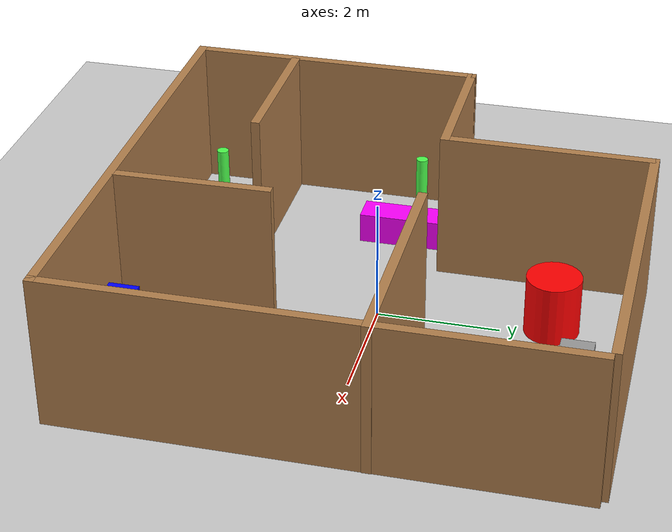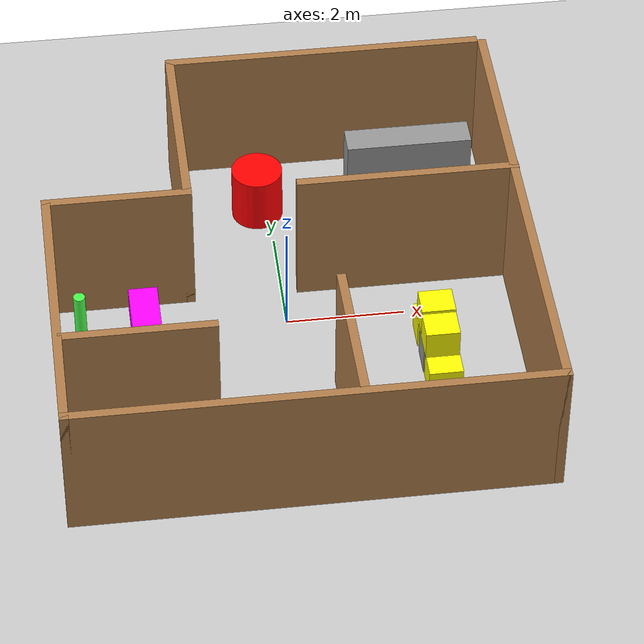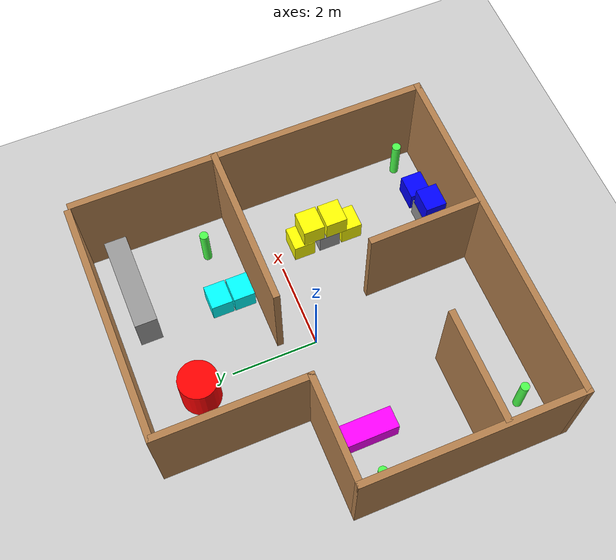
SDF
<sdf version="1.4">
 <world name="default">
  <light name="sun" type="directional">
   <pose>0 0 10 0 -0 0</pose>
   <diffuse>0.8 0.8 0.8 1</diffuse>
   <specular>0.2 0.2 0.2 1</specular>
   <attenuation>
    <range>1000</range>
    <constant>0.9</constant>
    <linear>0.01</linear>
    <quadratic>0.001</quadratic>
   </attenuation>
   <direction>0.5 0.1 -0.9</direction>
  </light>
  <model name="ground_plane">
   <static>1</static>
   <link name="link">
    <collision name="collision">
     <geometry><plane><normal>0 0 1</normal><size>100 100</size></plane></geometry>
     <surface><friction><ode><mu>100</mu><mu2>50</mu2></ode></friction></surface>
    </collision>
    <visual name="visual">
     <cast_shadows>0</cast_shadows>
     <geometry><plane><normal>0 0 1</normal><size>100 100</size></plane></geometry>
     <material>
      <script><uri>file://media/materials/scripts/gazebo.material</uri><name>Gazebo/Grey</name></script>
     </material>
    </visual>
    <velocity_decay><linear>0</linear><angular>0</angular></velocity_decay>
   </link>
  </model>
  <scene><ambient>0.4 0.4 0.4 1</ambient><background>0.7 0.7 0.7 1</background><shadows>0</shadows></scene>
  <physics type="ode">
   <max_step_size>0.01</max_step_size>
   <real_time_factor>1</real_time_factor>
   <real_time_update_rate>0</real_time_update_rate>
   <gravity>0 0 -9.8</gravity>
  </physics>
  <include><uri>model://RoomHouse</uri></include>
 </world>
</sdf>

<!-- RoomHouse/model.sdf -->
<sdf version='1.6'>
  <model name='RoomHouse'>
    <link name='Wall_0'>
      <pose frame=''>-3.92876 -1.675 0 0 -0 1.5708</pose>
      <self_collide>0</self_collide>
      <enable_wind>0</enable_wind>
      <kinematic>0</kinematic>
      <visual name='Wall_0_Visual'>
        <pose frame=''>0 0 1.25 0 -0 0</pose>
        <geometry>
          <box>
            <size>5 0.15 2.5</size>
          </box>
        </geometry>
        <material>
          <script>
            <uri>file://media/materials/scripts/gazebo.material</uri>
            <name>Gazebo/Wood</name>
          </script>
          <ambient>1 1 1 1</ambient>
        </material>
        <meta>
          <layer>0</layer>
        </meta>
        <transparency>0</transparency>
        <cast_shadows>1</cast_shadows>
      </visual>
      <collision name='Wall_0_Collision'>
        <laser_retro>0</laser_retro>
        <max_contacts>10</max_contacts>
        <pose frame=''>0 0 1.25 0 -0 0</pose>
        <geometry>
          <box>
            <size>5 0.15 2.5</size>
          </box>
        </geometry>
        <surface>
          <friction>
            <ode>
              <mu>1</mu>
              <mu2>1</mu2>
              <fdir1>0 0 0</fdir1>
              <slip1>0</slip1>
              <slip2>0</slip2>
            </ode>
            <torsional>
              <coefficient>1</coefficient>
              <patch_radius>0</patch_radius>
              <surface_radius>0</surface_radius>
              <use_patch_radius>1</use_patch_radius>
              <ode>
                <slip>0</slip>
              </ode>
            </torsional>
          </friction>
          <bounce>
            <restitution_coefficient>0</restitution_coefficient>
            <threshold>1e+06</threshold>
          </bounce>
          <contact>
            <collide_without_contact>0</collide_without_contact>
            <collide_without_contact_bitmask>1</collide_without_contact_bitmask>
            <collide_bitmask>1</collide_bitmask>
            <ode>
              <soft_cfm>0</soft_cfm>
              <soft_erp>0.2</soft_erp>
              <kp>1e+13</kp>
              <kd>1</kd>
              <max_vel>0.01</max_vel>
              <min_depth>0</min_depth>
            </ode>
            <bullet>
              <split_impulse>1</split_impulse>
              <split_impulse_penetration_threshold>-0.01</split_impulse_penetration_threshold>
              <soft_cfm>0</soft_cfm>
              <soft_erp>0.2</soft_erp>
              <kp>1e+13</kp>
              <kd>1</kd>
            </bullet>
          </contact>
        </surface>
      </collision>
    </link>
    <link name='Wall_12'>
      <pose frame=''>2.12876 0.762181 0 0 -0 3.14159</pose>
      <self_collide>0</self_collide>
      <enable_wind>0</enable_wind>
      <kinematic>0</kinematic>
      <visual name='Wall_12_Visual'>
        <pose frame=''>0 0 1.25 0 -0 0</pose>
        <geometry>
          <box>
            <size>3.75 0.15 2.5</size>
          </box>
        </geometry>
        <material>
          <script>
            <uri>file://media/materials/scripts/gazebo.material</uri>
            <name>Gazebo/Wood</name>
          </script>
          <ambient>1 1 1 1</ambient>
        </material>
        <meta>
          <layer>0</layer>
        </meta>
        <transparency>0</transparency>
        <cast_shadows>1</cast_shadows>
      </visual>
      <collision name='Wall_12_Collision'>
        <laser_retro>0</laser_retro>
        <max_contacts>10</max_contacts>
        <pose frame=''>0 0 1.25 0 -0 0</pose>
        <geometry>
          <box>
            <size>3.75 0.15 2.5</size>
          </box>
        </geometry>
        <surface>
          <friction>
            <ode>
              <mu>1</mu>
              <mu2>1</mu2>
              <fdir1>0 0 0</fdir1>
              <slip1>0</slip1>
              <slip2>0</slip2>
            </ode>
            <torsional>
              <coefficient>1</coefficient>
              <patch_radius>0</patch_radius>
              <surface_radius>0</surface_radius>
              <use_patch_radius>1</use_patch_radius>
              <ode>
                <slip>0</slip>
              </ode>
            </torsional>
          </friction>
          <bounce>
            <restitution_coefficient>0</restitution_coefficient>
            <threshold>1e+06</threshold>
          </bounce>
          <contact>
            <collide_without_contact>0</collide_without_contact>
            <collide_without_contact_bitmask>1</collide_without_contact_bitmask>
            <collide_bitmask>1</collide_bitmask>
            <ode>
              <soft_cfm>0</soft_cfm>
              <soft_erp>0.2</soft_erp>
              <kp>1e+13</kp>
              <kd>1</kd>
              <max_vel>0.01</max_vel>
              <min_depth>0</min_depth>
            </ode>
            <bullet>
              <split_impulse>1</split_impulse>
              <split_impulse_penetration_threshold>-0.01</split_impulse_penetration_threshold>
              <soft_cfm>0</soft_cfm>
              <soft_erp>0.2</soft_erp>
              <kp>1e+13</kp>
              <kd>1</kd>
            </bullet>
          </contact>
        </surface>
      </collision>
    </link>
    <link name='Wall_12_clone'>
      <pose frame=''>-2.64229 -2.37905 0 0 -0 3.14159</pose>
      <self_collide>0</self_collide>
      <enable_wind>0</enable_wind>
      <kinematic>0</kinematic>
      <inertial>
        <inertia>
          <ixx>0</ixx>
          <ixy>0</ixy>
          <ixz>0</ixz>
          <iyy>0</iyy>
          <iyz>0</iyz>
          <izz>0</izz>
        </inertia>
        <mass>0</mass>
        <pose frame=''>0 0 0 0 -0 0</pose>
      </inertial>
      <visual name='Wall_12_Visual'>
        <pose frame=''>0 0 1.25 0 -0 0</pose>
        <geometry>
          <box>
            <size>2.54886 0.15 2.5</size>
          </box>
        </geometry>
        <material>
          <script>
            <uri>file://media/materials/scripts/gazebo.material</uri>
            <name>Gazebo/Wood</name>
          </script>
          <ambient>1 1 1 1</ambient>
          <shader type='pixel'/>
        </material>
        <meta>
          <layer>0</layer>
        </meta>
        <transparency>0</transparency>
        <cast_shadows>1</cast_shadows>
      </visual>
      <collision name='Wall_12_Collision'>
        <laser_retro>0</laser_retro>
        <max_contacts>10</max_contacts>
        <pose frame=''>0 0 1.25 0 -0 0</pose>
        <geometry>
          <box>
            <size>2.54886 0.15 2.5</size>
          </box>
        </geometry>
        <surface>
          <friction>
            <ode>
              <mu>1</mu>
              <mu2>1</mu2>
              <fdir1>0 0 0</fdir1>
              <slip1>0</slip1>
              <slip2>0</slip2>
            </ode>
            <torsional>
              <coefficient>1</coefficient>
              <patch_radius>0</patch_radius>
              <surface_radius>0</surface_radius>
              <use_patch_radius>1</use_patch_radius>
              <ode>
                <slip>0</slip>
              </ode>
            </torsional>
          </friction>
          <bounce>
            <restitution_coefficient>0</restitution_coefficient>
            <threshold>1e+06</threshold>
          </bounce>
          <contact>
            <collide_without_contact>0</collide_without_contact>
            <collide_without_contact_bitmask>1</collide_without_contact_bitmask>
            <collide_bitmask>1</collide_bitmask>
            <ode>
              <soft_cfm>0</soft_cfm>
              <soft_erp>0.2</soft_erp>
              <kp>1e+13</kp>
              <kd>1</kd>
              <max_vel>0.01</max_vel>
              <min_depth>0</min_depth>
            </ode>
            <bullet>
              <split_impulse>1</split_impulse>
              <split_impulse_penetration_threshold>-0.01</split_impulse_penetration_threshold>
              <soft_cfm>0</soft_cfm>
              <soft_erp>0.2</soft_erp>
              <kp>1e+13</kp>
              <kd>1</kd>
            </bullet>
          </contact>
        </surface>
      </collision>
    </link>
    <link name='Wall_12_clone_clone'>
      <pose frame=''>0.72508 -2.77455 0 0 -0 1.58655</pose>
      <self_collide>0</self_collide>
      <enable_wind>0</enable_wind>
      <kinematic>0</kinematic>
      <inertial>
        <inertia>
          <ixx>0</ixx>
          <ixy>0</ixy>
          <ixz>0</ixz>
          <iyy>0</iyy>
          <iyz>0</iyz>
          <izz>0</izz>
        </inertia>
        <mass>0</mass>
        <pose frame=''>0 0 0 0 -0 0</pose>
      </inertial>
      <visual name='Wall_12_Visual'>
        <pose frame=''>0 0 1.25 0 -0 0</pose>
        <geometry>
          <box>
            <size>2.54886 0.15 2.5</size>
          </box>
        </geometry>
        <material>
          <script>
            <uri>file://media/materials/scripts/gazebo.material</uri>
            <name>Gazebo/Wood</name>
          </script>
          <ambient>1 1 1 1</ambient>
          <shader type='pixel'/>
        </material>
        <meta>
          <layer>0</layer>
        </meta>
        <transparency>0</transparency>
        <cast_shadows>1</cast_shadows>
      </visual>
      <collision name='Wall_12_Collision'>
        <laser_retro>0</laser_retro>
        <max_contacts>10</max_contacts>
        <pose frame=''>0 0 1.25 0 -0 0</pose>
        <geometry>
          <box>
            <size>2.54886 0.15 2.5</size>
          </box>
        </geometry>
        <surface>
          <friction>
            <ode>
              <mu>1</mu>
              <mu2>1</mu2>
              <fdir1>0 0 0</fdir1>
              <slip1>0</slip1>
              <slip2>0</slip2>
            </ode>
            <torsional>
              <coefficient>1</coefficient>
              <patch_radius>0</patch_radius>
              <surface_radius>0</surface_radius>
              <use_patch_radius>1</use_patch_radius>
              <ode>
                <slip>0</slip>
              </ode>
            </torsional>
          </friction>
          <bounce>
            <restitution_coefficient>0</restitution_coefficient>
            <threshold>1e+06</threshold>
          </bounce>
          <contact>
            <collide_without_contact>0</collide_without_contact>
            <collide_without_contact_bitmask>1</collide_without_contact_bitmask>
            <collide_bitmask>1</collide_bitmask>
            <ode>
              <soft_cfm>0</soft_cfm>
              <soft_erp>0.2</soft_erp>
              <kp>1e+13</kp>
              <kd>1</kd>
              <max_vel>0.01</max_vel>
              <min_depth>0</min_depth>
            </ode>
            <bullet>
              <split_impulse>1</split_impulse>
              <split_impulse_penetration_threshold>-0.01</split_impulse_penetration_threshold>
              <soft_cfm>0</soft_cfm>
              <soft_erp>0.2</soft_erp>
              <kp>1e+13</kp>
              <kd>1</kd>
            </bullet>
          </contact>
        </surface>
      </collision>
    </link>
    <link name='Wall_2'>
      <pose frame=''>-0.003758 -4.1 0 0 -0 0</pose>
      <self_collide>0</self_collide>
      <enable_wind>0</enable_wind>
      <kinematic>0</kinematic>
      <visual name='Wall_2_Visual'>
        <pose frame=''>0 0 1.25 0 -0 0</pose>
        <geometry>
          <box>
            <size>8 0.15 2.5</size>
          </box>
        </geometry>
        <material>
          <script>
            <uri>file://media/materials/scripts/gazebo.material</uri>
            <name>Gazebo/Wood</name>
          </script>
          <ambient>1 1 1 1</ambient>
        </material>
        <meta>
          <layer>0</layer>
        </meta>
        <transparency>0</transparency>
        <cast_shadows>1</cast_shadows>
      </visual>
      <collision name='Wall_2_Collision'>
        <laser_retro>0</laser_retro>
        <max_contacts>10</max_contacts>
        <pose frame=''>0 0 1.25 0 -0 0</pose>
        <geometry>
          <box>
            <size>8 0.15 2.5</size>
          </box>
        </geometry>
        <surface>
          <friction>
            <ode>
              <mu>1</mu>
              <mu2>1</mu2>
              <fdir1>0 0 0</fdir1>
              <slip1>0</slip1>
              <slip2>0</slip2>
            </ode>
            <torsional>
              <coefficient>1</coefficient>
              <patch_radius>0</patch_radius>
              <surface_radius>0</surface_radius>
              <use_patch_radius>1</use_patch_radius>
              <ode>
                <slip>0</slip>
              </ode>
            </torsional>
          </friction>
          <bounce>
            <restitution_coefficient>0</restitution_coefficient>
            <threshold>1e+06</threshold>
          </bounce>
          <contact>
            <collide_without_contact>0</collide_without_contact>
            <collide_without_contact_bitmask>1</collide_without_contact_bitmask>
            <collide_bitmask>1</collide_bitmask>
            <ode>
              <soft_cfm>0</soft_cfm>
              <soft_erp>0.2</soft_erp>
              <kp>1e+13</kp>
              <kd>1</kd>
              <max_vel>0.01</max_vel>
              <min_depth>0</min_depth>
            </ode>
            <bullet>
              <split_impulse>1</split_impulse>
              <split_impulse_penetration_threshold>-0.01</split_impulse_penetration_threshold>
              <soft_cfm>0</soft_cfm>
              <soft_erp>0.2</soft_erp>
              <kp>1e+13</kp>
              <kd>1</kd>
            </bullet>
          </contact>
        </surface>
      </collision>
    </link>
    <link name='Wall_4'>
      <pose frame=''>3.92124 -0.05 0 0 -0 1.5708</pose>
      <self_collide>0</self_collide>
      <enable_wind>0</enable_wind>
      <kinematic>0</kinematic>
      <visual name='Wall_4_Visual'>
        <pose frame=''>0 0 1.25 0 -0 0</pose>
        <geometry>
          <box>
            <size>8.25 0.15 2.5</size>
          </box>
        </geometry>
        <material>
          <script>
            <uri>file://media/materials/scripts/gazebo.material</uri>
            <name>Gazebo/Wood</name>
          </script>
          <ambient>1 1 1 1</ambient>
        </material>
        <meta>
          <layer>0</layer>
        </meta>
        <transparency>0</transparency>
        <cast_shadows>1</cast_shadows>
      </visual>
      <collision name='Wall_4_Collision'>
        <laser_retro>0</laser_retro>
        <max_contacts>10</max_contacts>
        <pose frame=''>0 0 1.25 0 -0 0</pose>
        <geometry>
          <box>
            <size>8.25 0.15 2.5</size>
          </box>
        </geometry>
        <surface>
          <friction>
            <ode>
              <mu>1</mu>
              <mu2>1</mu2>
              <fdir1>0 0 0</fdir1>
              <slip1>0</slip1>
              <slip2>0</slip2>
            </ode>
            <torsional>
              <coefficient>1</coefficient>
              <patch_radius>0</patch_radius>
              <surface_radius>0</surface_radius>
              <use_patch_radius>1</use_patch_radius>
              <ode>
                <slip>0</slip>
              </ode>
            </torsional>
          </friction>
          <bounce>
            <restitution_coefficient>0</restitution_coefficient>
            <threshold>1e+06</threshold>
          </bounce>
          <contact>
            <collide_without_contact>0</collide_without_contact>
            <collide_without_contact_bitmask>1</collide_without_contact_bitmask>
            <collide_bitmask>1</collide_bitmask>
            <ode>
              <soft_cfm>0</soft_cfm>
              <soft_erp>0.2</soft_erp>
              <kp>1e+13</kp>
              <kd>1</kd>
              <max_vel>0.01</max_vel>
              <min_depth>0</min_depth>
            </ode>
            <bullet>
              <split_impulse>1</split_impulse>
              <split_impulse_penetration_threshold>-0.01</split_impulse_penetration_threshold>
              <soft_cfm>0</soft_cfm>
              <soft_erp>0.2</soft_erp>
              <kp>1e+13</kp>
              <kd>1</kd>
            </bullet>
          </contact>
        </surface>
      </collision>
    </link>
    <link name='Wall_6'>
      <pose frame=''>-2.75376 0.75 0 0 -0 0</pose>
      <self_collide>0</self_collide>
      <enable_wind>0</enable_wind>
      <kinematic>0</kinematic>
      <visual name='Wall_6_Visual'>
        <pose frame=''>0 0 1.25 0 -0 0</pose>
        <geometry>
          <box>
            <size>2.5 0.15 2.5</size>
          </box>
        </geometry>
        <material>
          <script>
            <uri>file://media/materials/scripts/gazebo.material</uri>
            <name>Gazebo/Wood</name>
          </script>
          <ambient>1 1 1 1</ambient>
        </material>
        <meta>
          <layer>0</layer>
        </meta>
        <transparency>0</transparency>
        <cast_shadows>1</cast_shadows>
      </visual>
      <collision name='Wall_6_Collision'>
        <laser_retro>0</laser_retro>
        <max_contacts>10</max_contacts>
        <pose frame=''>0 0 1.25 0 -0 0</pose>
        <geometry>
          <box>
            <size>2.5 0.15 2.5</size>
          </box>
        </geometry>
        <surface>
          <friction>
            <ode>
              <mu>1</mu>
              <mu2>1</mu2>
              <fdir1>0 0 0</fdir1>
              <slip1>0</slip1>
              <slip2>0</slip2>
            </ode>
            <torsional>
              <coefficient>1</coefficient>
              <patch_radius>0</patch_radius>
              <surface_radius>0</surface_radius>
              <use_patch_radius>1</use_patch_radius>
              <ode>
                <slip>0</slip>
              </ode>
            </torsional>
          </friction>
          <bounce>
            <restitution_coefficient>0</restitution_coefficient>
            <threshold>1e+06</threshold>
          </bounce>
          <contact>
            <collide_without_contact>0</collide_without_contact>
            <collide_without_contact_bitmask>1</collide_without_contact_bitmask>
            <collide_bitmask>1</collide_bitmask>
            <ode>
              <soft_cfm>0</soft_cfm>
              <soft_erp>0.2</soft_erp>
              <kp>1e+13</kp>
              <kd>1</kd>
              <max_vel>0.01</max_vel>
              <min_depth>0</min_depth>
            </ode>
            <bullet>
              <split_impulse>1</split_impulse>
              <split_impulse_penetration_threshold>-0.01</split_impulse_penetration_threshold>
              <soft_cfm>0</soft_cfm>
              <soft_erp>0.2</soft_erp>
              <kp>1e+13</kp>
              <kd>1</kd>
            </bullet>
          </contact>
        </surface>
      </collision>
    </link>
    <link name='Wall_8'>
      <pose frame=''>-1.57876 2.425 0 0 -0 1.5708</pose>
      <self_collide>0</self_collide>
      <enable_wind>0</enable_wind>
      <kinematic>0</kinematic>
      <visual name='Wall_8_Visual'>
        <pose frame=''>0 0 1.25 0 -0 0</pose>
        <geometry>
          <box>
            <size>3.5 0.15 2.5</size>
          </box>
        </geometry>
        <material>
          <script>
            <uri>file://media/materials/scripts/gazebo.material</uri>
            <name>Gazebo/Wood</name>
          </script>
          <ambient>1 1 1 1</ambient>
        </material>
        <meta>
          <layer>0</layer>
        </meta>
        <transparency>0</transparency>
        <cast_shadows>1</cast_shadows>
      </visual>
      <collision name='Wall_8_Collision'>
        <laser_retro>0</laser_retro>
        <max_contacts>10</max_contacts>
        <pose frame=''>0 0 1.25 0 -0 0</pose>
        <geometry>
          <box>
            <size>3.5 0.15 2.5</size>
          </box>
        </geometry>
        <surface>
          <friction>
            <ode>
              <mu>1</mu>
              <mu2>1</mu2>
              <fdir1>0 0 0</fdir1>
              <slip1>0</slip1>
              <slip2>0</slip2>
            </ode>
            <torsional>
              <coefficient>1</coefficient>
              <patch_radius>0</patch_radius>
              <surface_radius>0</surface_radius>
              <use_patch_radius>1</use_patch_radius>
              <ode>
                <slip>0</slip>
              </ode>
            </torsional>
          </friction>
          <bounce>
            <restitution_coefficient>0</restitution_coefficient>
            <threshold>1e+06</threshold>
          </bounce>
          <contact>
            <collide_without_contact>0</collide_without_contact>
            <collide_without_contact_bitmask>1</collide_without_contact_bitmask>
            <collide_bitmask>1</collide_bitmask>
            <ode>
              <soft_cfm>0</soft_cfm>
              <soft_erp>0.2</soft_erp>
              <kp>1e+13</kp>
              <kd>1</kd>
              <max_vel>0.01</max_vel>
              <min_depth>0</min_depth>
            </ode>
            <bullet>
              <split_impulse>1</split_impulse>
              <split_impulse_penetration_threshold>-0.01</split_impulse_penetration_threshold>
              <soft_cfm>0</soft_cfm>
              <soft_erp>0.2</soft_erp>
              <kp>1e+13</kp>
              <kd>1</kd>
            </bullet>
          </contact>
        </surface>
      </collision>
    </link>
    <link name='Wall_9'>
      <pose frame=''>1.09624 4.1 0 0 -0 0</pose>
      <self_collide>0</self_collide>
      <enable_wind>0</enable_wind>
      <kinematic>0</kinematic>
      <visual name='Wall_9_Visual'>
        <pose frame=''>0 0 1.25 0 -0 0</pose>
        <geometry>
          <box>
            <size>5.5 0.15 2.5</size>
          </box>
        </geometry>
        <material>
          <script>
            <uri>file://media/materials/scripts/gazebo.material</uri>
            <name>Gazebo/Wood</name>
          </script>
          <ambient>1 1 1 1</ambient>
        </material>
        <meta>
          <layer>0</layer>
        </meta>
        <transparency>0</transparency>
        <cast_shadows>1</cast_shadows>
      </visual>
      <collision name='Wall_9_Collision'>
        <laser_retro>0</laser_retro>
        <max_contacts>10</max_contacts>
        <pose frame=''>0 0 1.25 0 -0 0</pose>
        <geometry>
          <box>
            <size>5.5 0.15 2.5</size>
          </box>
        </geometry>
        <surface>
          <friction>
            <ode>
              <mu>1</mu>
              <mu2>1</mu2>
              <fdir1>0 0 0</fdir1>
              <slip1>0</slip1>
              <slip2>0</slip2>
            </ode>
            <torsional>
              <coefficient>1</coefficient>
              <patch_radius>0</patch_radius>
              <surface_radius>0</surface_radius>
              <use_patch_radius>1</use_patch_radius>
              <ode>
                <slip>0</slip>
              </ode>
            </torsional>
          </friction>
          <bounce>
            <restitution_coefficient>0</restitution_coefficient>
            <threshold>1e+06</threshold>
          </bounce>
          <contact>
            <collide_without_contact>0</collide_without_contact>
            <collide_without_contact_bitmask>1</collide_without_contact_bitmask>
            <collide_bitmask>1</collide_bitmask>
            <ode>
              <soft_cfm>0</soft_cfm>
              <soft_erp>0.2</soft_erp>
              <kp>1e+13</kp>
              <kd>1</kd>
              <max_vel>0.01</max_vel>
              <min_depth>0</min_depth>
            </ode>
            <bullet>
              <split_impulse>1</split_impulse>
              <split_impulse_penetration_threshold>-0.01</split_impulse_penetration_threshold>
              <soft_cfm>0</soft_cfm>
              <soft_erp>0.2</soft_erp>
              <kp>1e+13</kp>
              <kd>1</kd>
            </bullet>
          </contact>
        </surface>
      </collision>
    </link>
    <link name='link_0'>
      <inertial>
        <mass>1.12546</mass>
        <inertia>
          <ixx>0.118193</ixx>
          <ixy>0</ixy>
          <ixz>0</ixz>
          <iyy>0.55036</iyy>
          <iyz>0</iyz>
          <izz>0.480977</izz>
        </inertia>
        <pose frame=''>0 0 0 0 -0 0</pose>
      </inertial>
      <pose frame=''>2.55096 3.38549 0.5 0 -0 0</pose>
      <gravity>1</gravity>
      <self_collide>0</self_collide>
      <kinematic>0</kinematic>
      <enable_wind>0</enable_wind>
      <visual name='visual'>
        <pose frame=''>0 0 0 0 -0 0</pose>
        <geometry>
          <box>
            <size>2.20638 0.510112 1</size>
          </box>
        </geometry>
        <material>
          <lighting>1</lighting>
          <script>
            <uri>file://media/materials/scripts/gazebo.material</uri>
            <name>Gazebo/Grey</name>
          </script>
          <ambient>0.5 0.5 0.5 0</ambient>
          <shader type='vertex'>
            <normal_map>__default__</normal_map>
          </shader>
          <diffuse>0.7 0.7 0.7 1</diffuse>
          <specular>0.01 0.01 0.01 1</specular>
          <emissive>0 0 0 1</emissive>
        </material>
        <transparency>0</transparency>
        <cast_shadows>1</cast_shadows>
      </visual>
      <collision name='collision'>
        <laser_retro>0</laser_retro>
        <max_contacts>10</max_contacts>
        <pose frame=''>0 0 0 0 -0 0</pose>
        <geometry>
          <box>
            <size>2.20638 0.510112 1</size>
          </box>
        </geometry>
        <surface>
          <friction>
            <ode>
              <mu>1</mu>
              <mu2>1</mu2>
              <fdir1>0 0 0</fdir1>
              <slip1>0</slip1>
              <slip2>0</slip2>
            </ode>
            <torsional>
              <coefficient>1</coefficient>
              <patch_radius>0</patch_radius>
              <surface_radius>0</surface_radius>
              <use_patch_radius>1</use_patch_radius>
              <ode>
                <slip>0</slip>
              </ode>
            </torsional>
          </friction>
          <bounce>
            <restitution_coefficient>0</restitution_coefficient>
            <threshold>1e+06</threshold>
          </bounce>
          <contact>
            <collide_without_contact>0</collide_without_contact>
            <collide_without_contact_bitmask>1</collide_without_contact_bitmask>
            <collide_bitmask>1</collide_bitmask>
            <ode>
              <soft_cfm>0</soft_cfm>
              <soft_erp>0.2</soft_erp>
              <kp>1e+13</kp>
              <kd>1</kd>
              <max_vel>0.01</max_vel>
              <min_depth>0</min_depth>
            </ode>
            <bullet>
              <split_impulse>1</split_impulse>
              <split_impulse_penetration_threshold>-0.01</split_impulse_penetration_threshold>
              <soft_cfm>0</soft_cfm>
              <soft_erp>0.2</soft_erp>
              <kp>1e+13</kp>
              <kd>1</kd>
            </bullet>
          </contact>
        </surface>
      </collision>
    </link>
    <link name='link_0_0'>
      <inertial>
        <mass>0.146602</mass>
        <inertia>
          <ixx>0.00626931</ixx>
          <ixy>0</ixy>
          <ixz>0</ixz>
          <iyy>0.00723583</iyy>
          <iyz>0</iyz>
          <izz>0.00701892</izz>
        </inertia>
        <pose frame=''>0 0 0 0 -0 0</pose>
      </inertial>
      <pose frame=''>1.3865 -3.62185 0.267544 0 -0 0</pose>
      <self_collide>0</self_collide>
      <enable_wind>0</enable_wind>
      <kinematic>0</kinematic>
      <gravity>1</gravity>
      <visual name='visual'>
        <pose frame=''>0 0 0 0 -0 0</pose>
        <geometry>
          <box>
            <size>0.571682 0.497702 0.51523</size>
          </box>
        </geometry>
        <material>
          <lighting>1</lighting>
          <script>
            <uri>file://media/materials/scripts/gazebo.material</uri>
            <name>Gazebo/Grey</name>
          </script>
          <ambient>0 0 1 0</ambient>
          <shader type='vertex'>
            <normal_map>__default__</normal_map>
          </shader>
          <diffuse>0.7 0.7 0.7 1</diffuse>
          <specular>0.01 0.01 0.01 1</specular>
          <emissive>0 0 0 1</emissive>
        </material>
        <transparency>0</transparency>
        <cast_shadows>1</cast_shadows>
      </visual>
      <collision name='collision'>
        <laser_retro>0</laser_retro>
        <max_contacts>10</max_contacts>
        <pose frame=''>0 0 0 0 -0 0</pose>
        <geometry>
          <box>
            <size>0.571682 0.497702 0.51523</size>
          </box>
        </geometry>
        <surface>
          <friction>
            <ode>
              <mu>1</mu>
              <mu2>1</mu2>
              <fdir1>0 0 0</fdir1>
              <slip1>0</slip1>
              <slip2>0</slip2>
            </ode>
            <torsional>
              <coefficient>1</coefficient>
              <patch_radius>0</patch_radius>
              <surface_radius>0</surface_radius>
              <use_patch_radius>1</use_patch_radius>
              <ode>
                <slip>0</slip>
              </ode>
            </torsional>
          </friction>
          <bounce>
            <restitution_coefficient>0</restitution_coefficient>
            <threshold>1e+06</threshold>
          </bounce>
          <contact>
            <collide_without_contact>0</collide_without_contact>
            <collide_without_contact_bitmask>1</collide_without_contact_bitmask>
            <collide_bitmask>1</collide_bitmask>
            <ode>
              <soft_cfm>0</soft_cfm>
              <soft_erp>0.2</soft_erp>
              <kp>1e+13</kp>
              <kd>1</kd>
              <max_vel>0.01</max_vel>
              <min_depth>0</min_depth>
            </ode>
            <bullet>
              <split_impulse>1</split_impulse>
              <split_impulse_penetration_threshold>-0.01</split_impulse_penetration_threshold>
              <soft_cfm>0</soft_cfm>
              <soft_erp>0.2</soft_erp>
              <kp>1e+13</kp>
              <kd>1</kd>
            </bullet>
          </contact>
        </surface>
      </collision>
    </link>
    <link name='link_0_0_clone'>
      <inertial>
        <mass>0.146602</mass>
        <inertia>
          <ixx>0.00626931</ixx>
          <ixy>0</ixy>
          <ixz>0</ixz>
          <iyy>0.00723583</iyy>
          <iyz>0</iyz>
          <izz>0.00701892</izz>
        </inertia>
        <pose frame=''>0 0 0 0 -0 0</pose>
      </inertial>
      <pose frame=''>1.96838 -3.64227 0.267544 0 -0 0</pose>
      <self_collide>0</self_collide>
      <enable_wind>0</enable_wind>
      <kinematic>0</kinematic>
      <visual name='visual_0'>
        <pose frame=''>0 0 0 0 -0 0</pose>
        <geometry>
          <box>
            <size>0.571682 0.497702 0.51523</size>
          </box>
        </geometry>
        <material>
          <lighting>1</lighting>
          <script>
            <uri>file://media/materials/scripts/gazebo.material</uri>
            <name>Gazebo/Grey</name>
          </script>
          <shader type='pixel'/>
        </material>
        <transparency>0</transparency>
        <cast_shadows>1</cast_shadows>
      </visual>
      <collision name='collision'>
        <laser_retro>0</laser_retro>
        <max_contacts>10</max_contacts>
        <pose frame=''>0 0 0 0 -0 0</pose>
        <geometry>
          <box>
            <size>0.571682 0.497702 0.51523</size>
          </box>
        </geometry>
        <surface>
          <friction>
            <ode>
              <mu>1</mu>
              <mu2>1</mu2>
              <fdir1>0 0 0</fdir1>
              <slip1>0</slip1>
              <slip2>0</slip2>
            </ode>
            <torsional>
              <coefficient>1</coefficient>
              <patch_radius>0</patch_radius>
              <surface_radius>0</surface_radius>
              <use_patch_radius>1</use_patch_radius>
              <ode>
                <slip>0</slip>
              </ode>
            </torsional>
          </friction>
          <bounce>
            <restitution_coefficient>0</restitution_coefficient>
            <threshold>1e+06</threshold>
          </bounce>
          <contact>
            <collide_without_contact>0</collide_without_contact>
            <collide_without_contact_bitmask>1</collide_without_contact_bitmask>
            <collide_bitmask>1</collide_bitmask>
            <ode>
              <soft_cfm>0</soft_cfm>
              <soft_erp>0.2</soft_erp>
              <kp>1e+13</kp>
              <kd>1</kd>
              <max_vel>0.01</max_vel>
              <min_depth>0</min_depth>
            </ode>
            <bullet>
              <split_impulse>1</split_impulse>
              <split_impulse_penetration_threshold>-0.01</split_impulse_penetration_threshold>
              <soft_cfm>0</soft_cfm>
              <soft_erp>0.2</soft_erp>
              <kp>1e+13</kp>
              <kd>1</kd>
            </bullet>
          </contact>
        </surface>
      </collision>
    </link>
    <link name='link_0_0_clone_clone'>
      <inertial>
        <mass>0.146602</mass>
        <inertia>
          <ixx>0.00626931</ixx>
          <ixy>0</ixy>
          <ixz>0</ixz>
          <iyy>0.00723583</iyy>
          <iyz>0</iyz>
          <izz>0.00701892</izz>
        </inertia>
        <pose frame=''>0 0 0 0 -0 0</pose>
      </inertial>
      <pose frame=''>2.63863 -3.64523 0.267544 0 -0 0</pose>
      <self_collide>0</self_collide>
      <enable_wind>0</enable_wind>
      <kinematic>0</kinematic>
      <gravity>1</gravity>
      <visual name='visual_0'>
        <pose frame=''>0 0 0 0 -0 0</pose>
        <geometry>
          <box>
            <size>0.571682 0.497702 0.51523</size>
          </box>
        </geometry>
        <material>
          <lighting>1</lighting>
          <script>
            <uri>file://media/materials/scripts/gazebo.material</uri>
            <name>Gazebo/Grey</name>
          </script>
          <shader type='pixel'>
            <normal_map>__default__</normal_map>
          </shader>
          <ambient>0 0 1 0</ambient>
          <diffuse>0.7 0.7 0.7 1</diffuse>
          <specular>0.01 0.01 0.01 1</specular>
          <emissive>0 0 0 1</emissive>
        </material>
        <transparency>0</transparency>
        <cast_shadows>1</cast_shadows>
      </visual>
      <collision name='collision'>
        <laser_retro>0</laser_retro>
        <max_contacts>10</max_contacts>
        <pose frame=''>0 0 0 0 -0 0</pose>
        <geometry>
          <box>
            <size>0.571682 0.497702 0.51523</size>
          </box>
        </geometry>
        <surface>
          <friction>
            <ode>
              <mu>1</mu>
              <mu2>1</mu2>
              <fdir1>0 0 0</fdir1>
              <slip1>0</slip1>
              <slip2>0</slip2>
            </ode>
            <torsional>
              <coefficient>1</coefficient>
              <patch_radius>0</patch_radius>
              <surface_radius>0</surface_radius>
              <use_patch_radius>1</use_patch_radius>
              <ode>
                <slip>0</slip>
              </ode>
            </torsional>
          </friction>
          <bounce>
            <restitution_coefficient>0</restitution_coefficient>
            <threshold>1e+06</threshold>
          </bounce>
          <contact>
            <collide_without_contact>0</collide_without_contact>
            <collide_without_contact_bitmask>1</collide_without_contact_bitmask>
            <collide_bitmask>1</collide_bitmask>
            <ode>
              <soft_cfm>0</soft_cfm>
              <soft_erp>0.2</soft_erp>
              <kp>1e+13</kp>
              <kd>1</kd>
              <max_vel>0.01</max_vel>
              <min_depth>0</min_depth>
            </ode>
            <bullet>
              <split_impulse>1</split_impulse>
              <split_impulse_penetration_threshold>-0.01</split_impulse_penetration_threshold>
              <soft_cfm>0</soft_cfm>
              <soft_erp>0.2</soft_erp>
              <kp>1e+13</kp>
              <kd>1</kd>
            </bullet>
          </contact>
        </surface>
      </collision>
    </link>
    <link name='link_0_0_clone_clone_0'>
      <inertial>
        <mass>0.146602</mass>
        <inertia>
          <ixx>0.00626931</ixx>
          <ixy>0</ixy>
          <ixz>0</ixz>
          <iyy>0.00723583</iyy>
          <iyz>0</iyz>
          <izz>0.00701892</izz>
        </inertia>
        <pose frame=''>0 0 0 0 -0 0</pose>
      </inertial>
      <pose frame=''>1.91455 -3.64943 0.784163 0 -0 0</pose>
      <self_collide>0</self_collide>
      <enable_wind>0</enable_wind>
      <kinematic>0</kinematic>
      <gravity>1</gravity>
      <visual name='visual_0'>
        <pose frame=''>0 0 0 0 -0 0</pose>
        <geometry>
          <box>
            <size>0.571682 0.497702 0.51523</size>
          </box>
        </geometry>
        <material>
          <lighting>1</lighting>
          <script>
            <uri>file://media/materials/scripts/gazebo.material</uri>
            <name>Gazebo/Grey</name>
          </script>
          <shader type='pixel'>
            <normal_map>__default__</normal_map>
          </shader>
          <ambient>0 0 1 0</ambient>
          <diffuse>0.7 0.7 0.7 1</diffuse>
          <specular>0.01 0.01 0.01 1</specular>
          <emissive>0 0 0 1</emissive>
        </material>
        <transparency>0</transparency>
        <cast_shadows>1</cast_shadows>
      </visual>
      <collision name='collision'>
        <laser_retro>0</laser_retro>
        <max_contacts>10</max_contacts>
        <pose frame=''>0 0 0 0 -0 0</pose>
        <geometry>
          <box>
            <size>0.571682 0.497702 0.51523</size>
          </box>
        </geometry>
        <surface>
          <friction>
            <ode>
              <mu>1</mu>
              <mu2>1</mu2>
              <fdir1>0 0 0</fdir1>
              <slip1>0</slip1>
              <slip2>0</slip2>
            </ode>
            <torsional>
              <coefficient>1</coefficient>
              <patch_radius>0</patch_radius>
              <surface_radius>0</surface_radius>
              <use_patch_radius>1</use_patch_radius>
              <ode>
                <slip>0</slip>
              </ode>
            </torsional>
          </friction>
          <bounce>
            <restitution_coefficient>0</restitution_coefficient>
            <threshold>1e+06</threshold>
          </bounce>
          <contact>
            <collide_without_contact>0</collide_without_contact>
            <collide_without_contact_bitmask>1</collide_without_contact_bitmask>
            <collide_bitmask>1</collide_bitmask>
            <ode>
              <soft_cfm>0</soft_cfm>
              <soft_erp>0.2</soft_erp>
              <kp>1e+13</kp>
              <kd>1</kd>
              <max_vel>0.01</max_vel>
              <min_depth>0</min_depth>
            </ode>
            <bullet>
              <split_impulse>1</split_impulse>
              <split_impulse_penetration_threshold>-0.01</split_impulse_penetration_threshold>
              <soft_cfm>0</soft_cfm>
              <soft_erp>0.2</soft_erp>
              <kp>1e+13</kp>
              <kd>1</kd>
            </bullet>
          </contact>
        </surface>
      </collision>
    </link>
    <link name='link_0_0_clone_clone_clone'>
      <inertial>
        <mass>0.146602</mass>
        <inertia>
          <ixx>0.00626931</ixx>
          <ixy>0</ixy>
          <ixz>0</ixz>
          <iyy>0.00723583</iyy>
          <iyz>0</iyz>
          <izz>0.00701892</izz>
        </inertia>
        <pose frame=''>0 0 0 0 -0 0</pose>
      </inertial>
      <pose frame=''>2.39989 -0.597576 0.267544 0 -0 0</pose>
      <self_collide>0</self_collide>
      <enable_wind>0</enable_wind>
      <kinematic>0</kinematic>
      <gravity>1</gravity>
      <visual name='visual_0'>
        <pose frame=''>0 0 0 0 -0 0</pose>
        <geometry>
          <box>
            <size>0.571682 0.497702 0.51523</size>
          </box>
        </geometry>
        <material>
          <lighting>1</lighting>
          <script>
            <uri>file://media/materials/scripts/gazebo.material</uri>
            <name>Gazebo/Grey</name>
          </script>
          <shader type='pixel'>
            <normal_map>__default__</normal_map>
          </shader>
          <ambient>1 1 0 1</ambient>
          <diffuse>0.7 0.7 0.7 1</diffuse>
          <specular>0.01 0.01 0.01 1</specular>
          <emissive>0 0 0 1</emissive>
        </material>
        <transparency>0</transparency>
        <cast_shadows>1</cast_shadows>
      </visual>
      <collision name='collision'>
        <laser_retro>0</laser_retro>
        <max_contacts>10</max_contacts>
        <pose frame=''>0 0 0 0 -0 0</pose>
        <geometry>
          <box>
            <size>0.571682 0.497702 0.51523</size>
          </box>
        </geometry>
        <surface>
          <friction>
            <ode>
              <mu>1</mu>
              <mu2>1</mu2>
              <fdir1>0 0 0</fdir1>
              <slip1>0</slip1>
              <slip2>0</slip2>
            </ode>
            <torsional>
              <coefficient>1</coefficient>
              <patch_radius>0</patch_radius>
              <surface_radius>0</surface_radius>
              <use_patch_radius>1</use_patch_radius>
              <ode>
                <slip>0</slip>
              </ode>
            </torsional>
          </friction>
          <bounce>
            <restitution_coefficient>0</restitution_coefficient>
            <threshold>1e+06</threshold>
          </bounce>
          <contact>
            <collide_without_contact>0</collide_without_contact>
            <collide_without_contact_bitmask>1</collide_without_contact_bitmask>
            <collide_bitmask>1</collide_bitmask>
            <ode>
              <soft_cfm>0</soft_cfm>
              <soft_erp>0.2</soft_erp>
              <kp>1e+13</kp>
              <kd>1</kd>
              <max_vel>0.01</max_vel>
              <min_depth>0</min_depth>
            </ode>
            <bullet>
              <split_impulse>1</split_impulse>
              <split_impulse_penetration_threshold>-0.01</split_impulse_penetration_threshold>
              <soft_cfm>0</soft_cfm>
              <soft_erp>0.2</soft_erp>
              <kp>1e+13</kp>
              <kd>1</kd>
            </bullet>
          </contact>
        </surface>
      </collision>
    </link>
    <link name='link_0_0_clone_clone_clone_clone'>
      <inertial>
        <mass>0.146602</mass>
        <inertia>
          <ixx>0.00626931</ixx>
          <ixy>0</ixy>
          <ixz>0</ixz>
          <iyy>0.00723583</iyy>
          <iyz>0</iyz>
          <izz>0.00701892</izz>
        </inertia>
        <pose frame=''>0 0 0 0 -0 0</pose>
      </inertial>
      <pose frame=''>2.40691 -1.21926 0.267544 0 -0 0</pose>
      <self_collide>0</self_collide>
      <enable_wind>0</enable_wind>
      <kinematic>0</kinematic>
      <visual name='visual_0'>
        <pose frame=''>0 0 0 0 -0 0</pose>
        <geometry>
          <box>
            <size>0.571682 0.497702 0.51523</size>
          </box>
        </geometry>
        <material>
          <lighting>1</lighting>
          <script>
            <uri>file://media/materials/scripts/gazebo.material</uri>
            <name>Gazebo/Grey</name>
          </script>
          <shader type='pixel'/>
        </material>
        <transparency>0</transparency>
        <cast_shadows>1</cast_shadows>
      </visual>
      <collision name='collision'>
        <laser_retro>0</laser_retro>
        <max_contacts>10</max_contacts>
        <pose frame=''>0 0 0 0 -0 0</pose>
        <geometry>
          <box>
            <size>0.571682 0.497702 0.51523</size>
          </box>
        </geometry>
        <surface>
          <friction>
            <ode>
              <mu>1</mu>
              <mu2>1</mu2>
              <fdir1>0 0 0</fdir1>
              <slip1>0</slip1>
              <slip2>0</slip2>
            </ode>
            <torsional>
              <coefficient>1</coefficient>
              <patch_radius>0</patch_radius>
              <surface_radius>0</surface_radius>
              <use_patch_radius>1</use_patch_radius>
              <ode>
                <slip>0</slip>
              </ode>
            </torsional>
          </friction>
          <bounce>
            <restitution_coefficient>0</restitution_coefficient>
            <threshold>1e+06</threshold>
          </bounce>
          <contact>
            <collide_without_contact>0</collide_without_contact>
            <collide_without_contact_bitmask>1</collide_without_contact_bitmask>
            <collide_bitmask>1</collide_bitmask>
            <ode>
              <soft_cfm>0</soft_cfm>
              <soft_erp>0.2</soft_erp>
              <kp>1e+13</kp>
              <kd>1</kd>
              <max_vel>0.01</max_vel>
              <min_depth>0</min_depth>
            </ode>
            <bullet>
              <split_impulse>1</split_impulse>
              <split_impulse_penetration_threshold>-0.01</split_impulse_penetration_threshold>
              <soft_cfm>0</soft_cfm>
              <soft_erp>0.2</soft_erp>
              <kp>1e+13</kp>
              <kd>1</kd>
            </bullet>
          </contact>
        </surface>
      </collision>
    </link>
    <link name='link_0_0_clone_clone_clone_clone_0'>
      <inertial>
        <mass>0.146602</mass>
        <inertia>
          <ixx>0.00626931</ixx>
          <ixy>0</ixy>
          <ixz>0</ixz>
          <iyy>0.00723583</iyy>
          <iyz>0</iyz>
          <izz>0.00701892</izz>
        </inertia>
        <pose frame=''>0 0 0 0 -0 0</pose>
      </inertial>
      <pose frame=''>2.41673 -1.77389 0.267544 0 -0 0</pose>
      <self_collide>0</self_collide>
      <enable_wind>0</enable_wind>
      <kinematic>0</kinematic>
      <gravity>1</gravity>
      <visual name='visual_0'>
        <pose frame=''>0 0 0 0 -0 0</pose>
        <geometry>
          <box>
            <size>0.571682 0.497702 0.51523</size>
          </box>
        </geometry>
        <material>
          <lighting>1</lighting>
          <script>
            <uri>file://media/materials/scripts/gazebo.material</uri>
            <name>Gazebo/Grey</name>
          </script>
          <shader type='pixel'>
            <normal_map>__default__</normal_map>
          </shader>
          <ambient>1 1 0 1</ambient>
          <diffuse>0.7 0.7 0.7 1</diffuse>
          <specular>0.01 0.01 0.01 1</specular>
          <emissive>0 0 0 1</emissive>
        </material>
        <transparency>0</transparency>
        <cast_shadows>1</cast_shadows>
      </visual>
      <collision name='collision'>
        <laser_retro>0</laser_retro>
        <max_contacts>10</max_contacts>
        <pose frame=''>0 0 0 0 -0 0</pose>
        <geometry>
          <box>
            <size>0.571682 0.497702 0.51523</size>
          </box>
        </geometry>
        <surface>
          <friction>
            <ode>
              <mu>1</mu>
              <mu2>1</mu2>
              <fdir1>0 0 0</fdir1>
              <slip1>0</slip1>
              <slip2>0</slip2>
            </ode>
            <torsional>
              <coefficient>1</coefficient>
              <patch_radius>0</patch_radius>
              <surface_radius>0</surface_radius>
              <use_patch_radius>1</use_patch_radius>
              <ode>
                <slip>0</slip>
              </ode>
            </torsional>
          </friction>
          <bounce>
            <restitution_coefficient>0</restitution_coefficient>
            <threshold>1e+06</threshold>
          </bounce>
          <contact>
            <collide_without_contact>0</collide_without_contact>
            <collide_without_contact_bitmask>1</collide_without_contact_bitmask>
            <collide_bitmask>1</collide_bitmask>
            <ode>
              <soft_cfm>0</soft_cfm>
              <soft_erp>0.2</soft_erp>
              <kp>1e+13</kp>
              <kd>1</kd>
              <max_vel>0.01</max_vel>
              <min_depth>0</min_depth>
            </ode>
            <bullet>
              <split_impulse>1</split_impulse>
              <split_impulse_penetration_threshold>-0.01</split_impulse_penetration_threshold>
              <soft_cfm>0</soft_cfm>
              <soft_erp>0.2</soft_erp>
              <kp>1e+13</kp>
              <kd>1</kd>
            </bullet>
          </contact>
        </surface>
      </collision>
    </link>
    <link name='link_0_0_clone_clone_clone_clone_1'>
      <inertial>
        <mass>0.35228</mass>
        <inertia>
          <ixx>0.0150649</ixx>
          <ixy>0</ixy>
          <ixz>0</ixz>
          <iyy>0.0631932</iyy>
          <iyz>0</iyz>
          <izz>0.062672</izz>
        </inertia>
        <pose frame=''>0 0 0 0 -0 0</pose>
      </inertial>
      <pose frame=''>-2.40533 -0.113674 0.267544 0 -0 1.57373</pose>
      <self_collide>0</self_collide>
      <enable_wind>0</enable_wind>
      <kinematic>0</kinematic>
      <gravity>1</gravity>
      <visual name='visual_0'>
        <pose frame=''>0 0 0 0 -0 0</pose>
        <geometry>
          <box>
            <size>1.37373 0.497702 0.51523</size>
          </box>
        </geometry>
        <material>
          <lighting>1</lighting>
          <script>
            <uri>file://media/materials/scripts/gazebo.material</uri>
            <name>Gazebo/Grey</name>
          </script>
          <shader type='pixel'>
            <normal_map>__default__</normal_map>
          </shader>
          <ambient>1 0 1 0</ambient>
          <diffuse>0.7 0.7 0.7 1</diffuse>
          <specular>0.01 0.01 0.01 1</specular>
          <emissive>0 0 0 1</emissive>
        </material>
        <transparency>0</transparency>
        <cast_shadows>1</cast_shadows>
      </visual>
      <collision name='collision'>
        <laser_retro>0</laser_retro>
        <max_contacts>10</max_contacts>
        <pose frame=''>0 0 0 0 -0 0</pose>
        <geometry>
          <box>
            <size>1.37373 0.497702 0.51523</size>
          </box>
        </geometry>
        <surface>
          <friction>
            <ode>
              <mu>1</mu>
              <mu2>1</mu2>
              <fdir1>0 0 0</fdir1>
              <slip1>0</slip1>
              <slip2>0</slip2>
            </ode>
            <torsional>
              <coefficient>1</coefficient>
              <patch_radius>0</patch_radius>
              <surface_radius>0</surface_radius>
              <use_patch_radius>1</use_patch_radius>
              <ode>
                <slip>0</slip>
              </ode>
            </torsional>
          </friction>
          <bounce>
            <restitution_coefficient>0</restitution_coefficient>
            <threshold>1e+06</threshold>
          </bounce>
          <contact>
            <collide_without_contact>0</collide_without_contact>
            <collide_without_contact_bitmask>1</collide_without_contact_bitmask>
            <collide_bitmask>1</collide_bitmask>
            <ode>
              <soft_cfm>0</soft_cfm>
              <soft_erp>0.2</soft_erp>
              <kp>1e+13</kp>
              <kd>1</kd>
              <max_vel>0.01</max_vel>
              <min_depth>0</min_depth>
            </ode>
            <bullet>
              <split_impulse>1</split_impulse>
              <split_impulse_penetration_threshold>-0.01</split_impulse_penetration_threshold>
              <soft_cfm>0</soft_cfm>
              <soft_erp>0.2</soft_erp>
              <kp>1e+13</kp>
              <kd>1</kd>
            </bullet>
          </contact>
        </surface>
      </collision>
    </link>
    <link name='link_0_0_clone_clone_clone_clone_2'>
      <inertial>
        <mass>0.146602</mass>
        <inertia>
          <ixx>0.00626931</ixx>
          <ixy>0</ixy>
          <ixz>0</ixz>
          <iyy>0.00723583</iyy>
          <iyz>0</iyz>
          <izz>0.00701892</izz>
        </inertia>
        <pose frame=''>0 0 0 0 -0 0</pose>
      </inertial>
      <pose frame=''>1.72465 1.66961 0.267544 0 -0 0</pose>
      <self_collide>0</self_collide>
      <enable_wind>0</enable_wind>
      <kinematic>0</kinematic>
      <gravity>1</gravity>
      <visual name='visual_0'>
        <pose frame=''>0 0 0 0 -0 0</pose>
        <geometry>
          <box>
            <size>0.571682 0.497702 0.51523</size>
          </box>
        </geometry>
        <material>
          <lighting>1</lighting>
          <script>
            <uri>file://media/materials/scripts/gazebo.material</uri>
            <name>Gazebo/Grey</name>
          </script>
          <shader type='pixel'>
            <normal_map>__default__</normal_map>
          </shader>
          <ambient>0 1 1 0</ambient>
          <diffuse>0.7 0.7 0.7 1</diffuse>
          <specular>0.01 0.01 0.01 1</specular>
          <emissive>0 0 0 1</emissive>
        </material>
        <transparency>0</transparency>
        <cast_shadows>1</cast_shadows>
      </visual>
      <collision name='collision'>
        <laser_retro>0</laser_retro>
        <max_contacts>10</max_contacts>
        <pose frame=''>0 0 0 0 -0 0</pose>
        <geometry>
          <box>
            <size>0.571682 0.497702 0.51523</size>
          </box>
        </geometry>
        <surface>
          <friction>
            <ode>
              <mu>1</mu>
              <mu2>1</mu2>
              <fdir1>0 0 0</fdir1>
              <slip1>0</slip1>
              <slip2>0</slip2>
            </ode>
            <torsional>
              <coefficient>1</coefficient>
              <patch_radius>0</patch_radius>
              <surface_radius>0</surface_radius>
              <use_patch_radius>1</use_patch_radius>
              <ode>
                <slip>0</slip>
              </ode>
            </torsional>
          </friction>
          <bounce>
            <restitution_coefficient>0</restitution_coefficient>
            <threshold>1e+06</threshold>
          </bounce>
          <contact>
            <collide_without_contact>0</collide_without_contact>
            <collide_without_contact_bitmask>1</collide_without_contact_bitmask>
            <collide_bitmask>1</collide_bitmask>
            <ode>
              <soft_cfm>0</soft_cfm>
              <soft_erp>0.2</soft_erp>
              <kp>1e+13</kp>
              <kd>1</kd>
              <max_vel>0.01</max_vel>
              <min_depth>0</min_depth>
            </ode>
            <bullet>
              <split_impulse>1</split_impulse>
              <split_impulse_penetration_threshold>-0.01</split_impulse_penetration_threshold>
              <soft_cfm>0</soft_cfm>
              <soft_erp>0.2</soft_erp>
              <kp>1e+13</kp>
              <kd>1</kd>
            </bullet>
          </contact>
        </surface>
      </collision>
    </link>
    <link name='link_0_0_clone_clone_clone_clone_2_clone'>
      <inertial>
        <mass>0.146602</mass>
        <inertia>
          <ixx>0.00626931</ixx>
          <ixy>0</ixy>
          <ixz>0</ixz>
          <iyy>0.00723583</iyy>
          <iyz>0</iyz>
          <izz>0.00701892</izz>
        </inertia>
        <pose frame=''>0 0 0 0 -0 0</pose>
      </inertial>
      <pose frame=''>1.72029 1.14355 0.267544 0 -0 0</pose>
      <self_collide>0</self_collide>
      <enable_wind>0</enable_wind>
      <kinematic>0</kinematic>
      <gravity>1</gravity>
      <visual name='visual_0'>
        <pose frame=''>0 0 0 0 -0 0</pose>
        <geometry>
          <box>
            <size>0.571682 0.497702 0.51523</size>
          </box>
        </geometry>
        <material>
          <lighting>1</lighting>
          <script>
            <uri>file://media/materials/scripts/gazebo.material</uri>
            <name>Gazebo/Grey</name>
          </script>
          <shader type='pixel'>
            <normal_map>__default__</normal_map>
          </shader>
          <ambient>0 1 1 0</ambient>
          <diffuse>0.7 0.7 0.7 1</diffuse>
          <specular>0.01 0.01 0.01 1</specular>
          <emissive>0 0 0 1</emissive>
        </material>
        <transparency>0</transparency>
        <cast_shadows>1</cast_shadows>
      </visual>
      <collision name='collision'>
        <laser_retro>0</laser_retro>
        <max_contacts>10</max_contacts>
        <pose frame=''>0 0 0 0 -0 0</pose>
        <geometry>
          <box>
            <size>0.571682 0.497702 0.51523</size>
          </box>
        </geometry>
        <surface>
          <friction>
            <ode>
              <mu>1</mu>
              <mu2>1</mu2>
              <fdir1>0 0 0</fdir1>
              <slip1>0</slip1>
              <slip2>0</slip2>
            </ode>
            <torsional>
              <coefficient>1</coefficient>
              <patch_radius>0</patch_radius>
              <surface_radius>0</surface_radius>
              <use_patch_radius>1</use_patch_radius>
              <ode>
                <slip>0</slip>
              </ode>
            </torsional>
          </friction>
          <bounce>
            <restitution_coefficient>0</restitution_coefficient>
            <threshold>1e+06</threshold>
          </bounce>
          <contact>
            <collide_without_contact>0</collide_without_contact>
            <collide_without_contact_bitmask>1</collide_without_contact_bitmask>
            <collide_bitmask>1</collide_bitmask>
            <ode>
              <soft_cfm>0</soft_cfm>
              <soft_erp>0.2</soft_erp>
              <kp>1e+13</kp>
              <kd>1</kd>
              <max_vel>0.01</max_vel>
              <min_depth>0</min_depth>
            </ode>
            <bullet>
              <split_impulse>1</split_impulse>
              <split_impulse_penetration_threshold>-0.01</split_impulse_penetration_threshold>
              <soft_cfm>0</soft_cfm>
              <soft_erp>0.2</soft_erp>
              <kp>1e+13</kp>
              <kd>1</kd>
            </bullet>
          </contact>
        </surface>
      </collision>
    </link>
    <link name='link_0_0_clone_clone_clone_clone_clone'>
      <inertial>
        <mass>0.146602</mass>
        <inertia>
          <ixx>0.00626931</ixx>
          <ixy>0</ixy>
          <ixz>0</ixz>
          <iyy>0.00723583</iyy>
          <iyz>0</iyz>
          <izz>0.00701892</izz>
        </inertia>
        <pose frame=''>0 0 0 0 -0 0</pose>
      </inertial>
      <pose frame=''>2.41599 -0.842118 0.788292 0 -0 0</pose>
      <self_collide>0</self_collide>
      <enable_wind>0</enable_wind>
      <kinematic>0</kinematic>
      <gravity>1</gravity>
      <visual name='visual_0'>
        <pose frame=''>0 0 0 0 -0 0</pose>
        <geometry>
          <box>
            <size>0.571682 0.497702 0.51523</size>
          </box>
        </geometry>
        <material>
          <lighting>1</lighting>
          <script>
            <uri>file://media/materials/scripts/gazebo.material</uri>
            <name>Gazebo/Grey</name>
          </script>
          <shader type='pixel'>
            <normal_map>__default__</normal_map>
          </shader>
          <ambient>1 1 0 0</ambient>
          <diffuse>0.7 0.7 0.7 1</diffuse>
          <specular>0.01 0.01 0.01 1</specular>
          <emissive>0 0 0 1</emissive>
        </material>
        <transparency>0</transparency>
        <cast_shadows>1</cast_shadows>
      </visual>
      <collision name='collision'>
        <laser_retro>0</laser_retro>
        <max_contacts>10</max_contacts>
        <pose frame=''>0 0 0 0 -0 0</pose>
        <geometry>
          <box>
            <size>0.571682 0.497702 0.51523</size>
          </box>
        </geometry>
        <surface>
          <friction>
            <ode>
              <mu>1</mu>
              <mu2>1</mu2>
              <fdir1>0 0 0</fdir1>
              <slip1>0</slip1>
              <slip2>0</slip2>
            </ode>
            <torsional>
              <coefficient>1</coefficient>
              <patch_radius>0</patch_radius>
              <surface_radius>0</surface_radius>
              <use_patch_radius>1</use_patch_radius>
              <ode>
                <slip>0</slip>
              </ode>
            </torsional>
          </friction>
          <bounce>
            <restitution_coefficient>0</restitution_coefficient>
            <threshold>1e+06</threshold>
          </bounce>
          <contact>
            <collide_without_contact>0</collide_without_contact>
            <collide_without_contact_bitmask>1</collide_without_contact_bitmask>
            <collide_bitmask>1</collide_bitmask>
            <ode>
              <soft_cfm>0</soft_cfm>
              <soft_erp>0.2</soft_erp>
              <kp>1e+13</kp>
              <kd>1</kd>
              <max_vel>0.01</max_vel>
              <min_depth>0</min_depth>
            </ode>
            <bullet>
              <split_impulse>1</split_impulse>
              <split_impulse_penetration_threshold>-0.01</split_impulse_penetration_threshold>
              <soft_cfm>0</soft_cfm>
              <soft_erp>0.2</soft_erp>
              <kp>1e+13</kp>
              <kd>1</kd>
            </bullet>
          </contact>
        </surface>
      </collision>
    </link>
    <link name='link_0_0_clone_clone_clone_clone_clone_clone'>
      <inertial>
        <mass>0.146602</mass>
        <inertia>
          <ixx>0.00626931</ixx>
          <ixy>0</ixy>
          <ixz>0</ixz>
          <iyy>0.00723583</iyy>
          <iyz>0</iyz>
          <izz>0.00701892</izz>
        </inertia>
        <pose frame=''>0 0 0 0 -0 0</pose>
      </inertial>
      <pose frame=''>2.4051 -1.38934 0.788292 0 -0 0</pose>
      <self_collide>0</self_collide>
      <enable_wind>0</enable_wind>
      <kinematic>0</kinematic>
      <gravity>1</gravity>
      <visual name='visual_0'>
        <pose frame=''>0 0 0 0 -0 0</pose>
        <geometry>
          <box>
            <size>0.571682 0.497702 0.51523</size>
          </box>
        </geometry>
        <material>
          <lighting>1</lighting>
          <script>
            <uri>file://media/materials/scripts/gazebo.material</uri>
            <name>Gazebo/Grey</name>
          </script>
          <shader type='pixel'>
            <normal_map>__default__</normal_map>
          </shader>
          <ambient>1 1 0 1</ambient>
          <diffuse>0.7 0.7 0.7 1</diffuse>
          <specular>0.01 0.01 0.01 1</specular>
          <emissive>0 0 0 1</emissive>
        </material>
        <transparency>0</transparency>
        <cast_shadows>1</cast_shadows>
      </visual>
      <collision name='collision'>
        <laser_retro>0</laser_retro>
        <max_contacts>10</max_contacts>
        <pose frame=''>0 0 0 0 -0 0</pose>
        <geometry>
          <box>
            <size>0.571682 0.497702 0.51523</size>
          </box>
        </geometry>
        <surface>
          <friction>
            <ode>
              <mu>1</mu>
              <mu2>1</mu2>
              <fdir1>0 0 0</fdir1>
              <slip1>0</slip1>
              <slip2>0</slip2>
            </ode>
            <torsional>
              <coefficient>1</coefficient>
              <patch_radius>0</patch_radius>
              <surface_radius>0</surface_radius>
              <use_patch_radius>1</use_patch_radius>
              <ode>
                <slip>0</slip>
              </ode>
            </torsional>
          </friction>
          <bounce>
            <restitution_coefficient>0</restitution_coefficient>
            <threshold>1e+06</threshold>
          </bounce>
          <contact>
            <collide_without_contact>0</collide_without_contact>
            <collide_without_contact_bitmask>1</collide_without_contact_bitmask>
            <collide_bitmask>1</collide_bitmask>
            <ode>
              <soft_cfm>0</soft_cfm>
              <soft_erp>0.2</soft_erp>
              <kp>1e+13</kp>
              <kd>1</kd>
              <max_vel>0.01</max_vel>
              <min_depth>0</min_depth>
            </ode>
            <bullet>
              <split_impulse>1</split_impulse>
              <split_impulse_penetration_threshold>-0.01</split_impulse_penetration_threshold>
              <soft_cfm>0</soft_cfm>
              <soft_erp>0.2</soft_erp>
              <kp>1e+13</kp>
              <kd>1</kd>
            </bullet>
          </contact>
        </surface>
      </collision>
    </link>
    <link name='link_0_1'>
      <inertial>
        <mass>0.0731269</mass>
        <inertia>
          <ixx>0.00642814</ixx>
          <ixy>0</ixy>
          <ixz>0</ixz>
          <iyy>0.00642814</iyy>
          <iyz>0</iyz>
          <izz>0.00066846</izz>
        </inertia>
        <pose frame=''>0 0 0 0 -0 0</pose>
      </inertial>
      <pose frame=''>3 1.5 0.5 0 -0 0</pose>
      <gravity>1</gravity>
      <self_collide>0</self_collide>
      <kinematic>0</kinematic>
      <enable_wind>0</enable_wind>
      <visual name='visual'>
        <pose frame=''>0 0 0 0 -0 0</pose>
        <geometry>
          <cylinder>
            <radius>0.1</radius>
            <length>1</length>
          </cylinder>
        </geometry>
        <material>
          <lighting>1</lighting>
          <script>
            <uri>file://media/materials/scripts/gazebo.material</uri>
            <name>Gazebo/Grey</name>
          </script>
          <shader type='vertex'>
            <normal_map>__default__</normal_map>
          </shader>
          <ambient>0.3 1 0.3 1</ambient>
          <diffuse>0.7 0.7 0.7 1</diffuse>
          <specular>0.01 0.01 0.01 1</specular>
          <emissive>0 0 0 1</emissive>
        </material>
        <transparency>0</transparency>
        <cast_shadows>1</cast_shadows>
      </visual>
      <collision name='collision'>
        <laser_retro>0</laser_retro>
        <max_contacts>10</max_contacts>
        <pose frame=''>0 0 0 0 -0 0</pose>
        <geometry>
          <cylinder>
            <radius>0.135212</radius>
            <length>1</length>
          </cylinder>
        </geometry>
        <surface>
          <friction>
            <ode>
              <mu>1</mu>
              <mu2>1</mu2>
              <fdir1>0 0 0</fdir1>
              <slip1>0</slip1>
              <slip2>0</slip2>
            </ode>
            <torsional>
              <coefficient>1</coefficient>
              <patch_radius>0</patch_radius>
              <surface_radius>0</surface_radius>
              <use_patch_radius>1</use_patch_radius>
              <ode>
                <slip>0</slip>
              </ode>
            </torsional>
          </friction>
          <bounce>
            <restitution_coefficient>0</restitution_coefficient>
            <threshold>1e+06</threshold>
          </bounce>
          <contact>
            <collide_without_contact>0</collide_without_contact>
            <collide_without_contact_bitmask>1</collide_without_contact_bitmask>
            <collide_bitmask>1</collide_bitmask>
            <ode>
              <soft_cfm>0</soft_cfm>
              <soft_erp>0.2</soft_erp>
              <kp>1e+13</kp>
              <kd>1</kd>
              <max_vel>0.01</max_vel>
              <min_depth>0</min_depth>
            </ode>
            <bullet>
              <split_impulse>1</split_impulse>
              <split_impulse_penetration_threshold>-0.01</split_impulse_penetration_threshold>
              <soft_cfm>0</soft_cfm>
              <soft_erp>0.2</soft_erp>
              <kp>1e+13</kp>
              <kd>1</kd>
            </bullet>
          </contact>
        </surface>
      </collision>
    </link>
    <link name='link_0_1_clone'>
      <inertial>
        <mass>0.0731269</mass>
        <inertia>
          <ixx>0.00642814</ixx>
          <ixy>0</ixy>
          <ixz>0</ixz>
          <iyy>0.00642814</iyy>
          <iyz>0</iyz>
          <izz>0.00066846</izz>
        </inertia>
        <pose frame=''>0 0 0 0 -0 0</pose>
      </inertial>
      <pose frame=''>3.5 -3.5 0.5 0 -0 0</pose>
      <gravity>1</gravity>
      <self_collide>0</self_collide>
      <kinematic>0</kinematic>
      <enable_wind>0</enable_wind>
      <visual name='visual_0'>
        <pose frame=''>0 0 0 0 -0 0</pose>
        <geometry>
          <cylinder>
            <radius>0.1</radius>
            <length>1</length>
          </cylinder>
        </geometry>
        <material>
          <lighting>1</lighting>
          <script>
            <uri>file://media/materials/scripts/gazebo.material</uri>
            <name>Gazebo/Grey</name>
          </script>
          <shader type='vertex'>
            <normal_map>__default__</normal_map>
          </shader>
          <ambient>0.3 1 0.3 1</ambient>
          <diffuse>0.7 0.7 0.7 1</diffuse>
          <specular>0.01 0.01 0.01 1</specular>
          <emissive>0 0 0 1</emissive>
        </material>
        <transparency>0</transparency>
        <cast_shadows>1</cast_shadows>
      </visual>
      <collision name='collision'>
        <laser_retro>0</laser_retro>
        <max_contacts>10</max_contacts>
        <pose frame=''>0 0 0 0 -0 0</pose>
        <geometry>
          <cylinder>
            <radius>0.135212</radius>
            <length>1</length>
          </cylinder>
        </geometry>
        <surface>
          <friction>
            <ode>
              <mu>1</mu>
              <mu2>1</mu2>
              <fdir1>0 0 0</fdir1>
              <slip1>0</slip1>
              <slip2>0</slip2>
            </ode>
            <torsional>
              <coefficient>1</coefficient>
              <patch_radius>0</patch_radius>
              <surface_radius>0</surface_radius>
              <use_patch_radius>1</use_patch_radius>
              <ode>
                <slip>0</slip>
              </ode>
            </torsional>
          </friction>
          <bounce>
            <restitution_coefficient>0</restitution_coefficient>
            <threshold>1e+06</threshold>
          </bounce>
          <contact>
            <collide_without_contact>0</collide_without_contact>
            <collide_without_contact_bitmask>1</collide_without_contact_bitmask>
            <collide_bitmask>1</collide_bitmask>
            <ode>
              <soft_cfm>0</soft_cfm>
              <soft_erp>0.2</soft_erp>
              <kp>1e+13</kp>
              <kd>1</kd>
              <max_vel>0.01</max_vel>
              <min_depth>0</min_depth>
            </ode>
            <bullet>
              <split_impulse>1</split_impulse>
              <split_impulse_penetration_threshold>-0.01</split_impulse_penetration_threshold>
              <soft_cfm>0</soft_cfm>
              <soft_erp>0.2</soft_erp>
              <kp>1e+13</kp>
              <kd>1</kd>
            </bullet>
          </contact>
        </surface>
      </collision>
    </link>
    <link name='link_0_1_clone_0'>
      <inertial>
        <mass>0.0731269</mass>
        <inertia>
          <ixx>0.00642814</ixx>
          <ixy>0</ixy>
          <ixz>0</ixz>
          <iyy>0.00642814</iyy>
          <iyz>0</iyz>
          <izz>0.00066846</izz>
        </inertia>
        <pose frame=''>0 0 0 0 -0 0</pose>
      </inertial>
      <pose frame=''>-3.5 0 0.5 0 -0 0</pose>
      <gravity>1</gravity>
      <self_collide>0</self_collide>
      <kinematic>0</kinematic>
      <enable_wind>0</enable_wind>
      <visual name='visual_0'>
        <pose frame=''>0 0 0 0 -0 0</pose>
        <geometry>
          <cylinder>
            <radius>0.1</radius>
            <length>1</length>
          </cylinder>
        </geometry>
        <material>
          <lighting>1</lighting>
          <script>
            <uri>file://media/materials/scripts/gazebo.material</uri>
            <name>Gazebo/Grey</name>
          </script>
          <shader type='vertex'>
            <normal_map>__default__</normal_map>
          </shader>
          <ambient>0.3 1 0.3 1</ambient>
          <diffuse>0.7 0.7 0.7 1</diffuse>
          <specular>0.01 0.01 0.01 1</specular>
          <emissive>0 0 0 1</emissive>
        </material>
        <transparency>0</transparency>
        <cast_shadows>1</cast_shadows>
      </visual>
      <collision name='collision'>
        <laser_retro>0</laser_retro>
        <max_contacts>10</max_contacts>
        <pose frame=''>0 0 0 0 -0 0</pose>
        <geometry>
          <cylinder>
            <radius>0.135212</radius>
            <length>1</length>
          </cylinder>
        </geometry>
        <surface>
          <friction>
            <ode>
              <mu>1</mu>
              <mu2>1</mu2>
              <fdir1>0 0 0</fdir1>
              <slip1>0</slip1>
              <slip2>0</slip2>
            </ode>
            <torsional>
              <coefficient>1</coefficient>
              <patch_radius>0</patch_radius>
              <surface_radius>0</surface_radius>
              <use_patch_radius>1</use_patch_radius>
              <ode>
                <slip>0</slip>
              </ode>
            </torsional>
          </friction>
          <bounce>
            <restitution_coefficient>0</restitution_coefficient>
            <threshold>1e+06</threshold>
          </bounce>
          <contact>
            <collide_without_contact>0</collide_without_contact>
            <collide_without_contact_bitmask>1</collide_without_contact_bitmask>
            <collide_bitmask>1</collide_bitmask>
            <ode>
              <soft_cfm>0</soft_cfm>
              <soft_erp>0.2</soft_erp>
              <kp>1e+13</kp>
              <kd>1</kd>
              <max_vel>0.01</max_vel>
              <min_depth>0</min_depth>
            </ode>
            <bullet>
              <split_impulse>1</split_impulse>
              <split_impulse_penetration_threshold>-0.01</split_impulse_penetration_threshold>
              <soft_cfm>0</soft_cfm>
              <soft_erp>0.2</soft_erp>
              <kp>1e+13</kp>
              <kd>1</kd>
            </bullet>
          </contact>
        </surface>
      </collision>
    </link>
    <link name='link_0_1_clone_1'>
      <inertial>
        <mass>0.0731269</mass>
        <inertia>
          <ixx>0.00642814</ixx>
          <ixy>0</ixy>
          <ixz>0</ixz>
          <iyy>0.00642814</iyy>
          <iyz>0</iyz>
          <izz>0.00066846</izz>
        </inertia>
        <pose frame=''>0 0 0 0 -0 0</pose>
      </inertial>
      <pose frame=''>-3 -3.5 0.5 0 -0 0</pose>
      <gravity>1</gravity>
      <self_collide>0</self_collide>
      <kinematic>0</kinematic>
      <enable_wind>0</enable_wind>
      <visual name='visual_0'>
        <pose frame=''>0 0 0 0 -0 0</pose>
        <geometry>
          <cylinder>
            <radius>0.1</radius>
            <length>1</length>
          </cylinder>
        </geometry>
        <material>
          <lighting>1</lighting>
          <script>
            <uri>file://media/materials/scripts/gazebo.material</uri>
            <name>Gazebo/Grey</name>
          </script>
          <shader type='vertex'>
            <normal_map>__default__</normal_map>
          </shader>
          <ambient>0.3 1 0.3 1</ambient>
          <diffuse>0.7 0.7 0.7 1</diffuse>
          <specular>0.01 0.01 0.01 1</specular>
          <emissive>0 0 0 1</emissive>
        </material>
        <transparency>0</transparency>
        <cast_shadows>1</cast_shadows>
      </visual>
      <collision name='collision'>
        <laser_retro>0</laser_retro>
        <max_contacts>10</max_contacts>
        <pose frame=''>0 0 0 0 -0 0</pose>
        <geometry>
          <cylinder>
            <radius>0.135212</radius>
            <length>1</length>
          </cylinder>
        </geometry>
        <surface>
          <friction>
            <ode>
              <mu>1</mu>
              <mu2>1</mu2>
              <fdir1>0 0 0</fdir1>
              <slip1>0</slip1>
              <slip2>0</slip2>
            </ode>
            <torsional>
              <coefficient>1</coefficient>
              <patch_radius>0</patch_radius>
              <surface_radius>0</surface_radius>
              <use_patch_radius>1</use_patch_radius>
              <ode>
                <slip>0</slip>
              </ode>
            </torsional>
          </friction>
          <bounce>
            <restitution_coefficient>0</restitution_coefficient>
            <threshold>1e+06</threshold>
          </bounce>
          <contact>
            <collide_without_contact>0</collide_without_contact>
            <collide_without_contact_bitmask>1</collide_without_contact_bitmask>
            <collide_bitmask>1</collide_bitmask>
            <ode>
              <soft_cfm>0</soft_cfm>
              <soft_erp>0.2</soft_erp>
              <kp>1e+13</kp>
              <kd>1</kd>
              <max_vel>0.01</max_vel>
              <min_depth>0</min_depth>
            </ode>
            <bullet>
              <split_impulse>1</split_impulse>
              <split_impulse_penetration_threshold>-0.01</split_impulse_penetration_threshold>
              <soft_cfm>0</soft_cfm>
              <soft_erp>0.2</soft_erp>
              <kp>1e+13</kp>
              <kd>1</kd>
            </bullet>
          </contact>
        </surface>
      </collision>
    </link>
    <link name='link_3'>
      <inertial>
        <mass>0.794577</mass>
        <inertia>
          <ixx>0.105674</ixx>
          <ixy>0</ixy>
          <ixz>0</ixz>
          <iyy>0.105674</iyy>
          <iyz>0</iyz>
          <izz>0.0789186</izz>
        </inertia>
        <pose frame=''>0 0 0 0 -0 0</pose>
      </inertial>
      <pose frame=''>-0.204584 2.79767 0.500733 0 -0 0</pose>
      <self_collide>0</self_collide>
      <enable_wind>0</enable_wind>
      <kinematic>0</kinematic>
      <gravity>1</gravity>
      <visual name='visual'>
        <pose frame=''>0 0 0 0 -0 0</pose>
        <geometry>
          <cylinder>
            <radius>0.445694</radius>
            <length>1</length>
          </cylinder>
        </geometry>
        <material>
          <lighting>1</lighting>
          <script>
            <uri>file://media/materials/scripts/gazebo.material</uri>
            <name>Gazebo/Grey</name>
          </script>
          <shader type='vertex'>
            <normal_map>__default__</normal_map>
          </shader>
          <ambient>1 0 0 1</ambient>
          <diffuse>0.7 0.7 0.7 1</diffuse>
          <specular>0.01 0.01 0.01 1</specular>
          <emissive>0 0 0 1</emissive>
        </material>
        <transparency>0</transparency>
        <cast_shadows>1</cast_shadows>
      </visual>
      <collision name='collision'>
        <laser_retro>0</laser_retro>
        <max_contacts>10</max_contacts>
        <pose frame=''>0 0 0 0 -0 0</pose>
        <geometry>
          <cylinder>
            <radius>0.445694</radius>
            <length>1</length>
          </cylinder>
        </geometry>
        <surface>
          <friction>
            <ode>
              <mu>1</mu>
              <mu2>1</mu2>
              <fdir1>0 0 0</fdir1>
              <slip1>0</slip1>
              <slip2>0</slip2>
            </ode>
            <torsional>
              <coefficient>1</coefficient>
              <patch_radius>0</patch_radius>
              <surface_radius>0</surface_radius>
              <use_patch_radius>1</use_patch_radius>
              <ode>
                <slip>0</slip>
              </ode>
            </torsional>
          </friction>
          <bounce>
            <restitution_coefficient>0</restitution_coefficient>
            <threshold>1e+06</threshold>
          </bounce>
          <contact>
            <collide_without_contact>0</collide_without_contact>
            <collide_without_contact_bitmask>1</collide_without_contact_bitmask>
            <collide_bitmask>1</collide_bitmask>
            <ode>
              <soft_cfm>0</soft_cfm>
              <soft_erp>0.2</soft_erp>
              <kp>1e+13</kp>
              <kd>1</kd>
              <max_vel>0.01</max_vel>
              <min_depth>0</min_depth>
            </ode>
            <bullet>
              <split_impulse>1</split_impulse>
              <split_impulse_penetration_threshold>-0.01</split_impulse_penetration_threshold>
              <soft_cfm>0</soft_cfm>
              <soft_erp>0.2</soft_erp>
              <kp>1e+13</kp>
              <kd>1</kd>
            </bullet>
          </contact>
        </surface>
      </collision>
    </link>
    <static>1</static>
    <allow_auto_disable>1</allow_auto_disable>
  </model>
</sdf>
